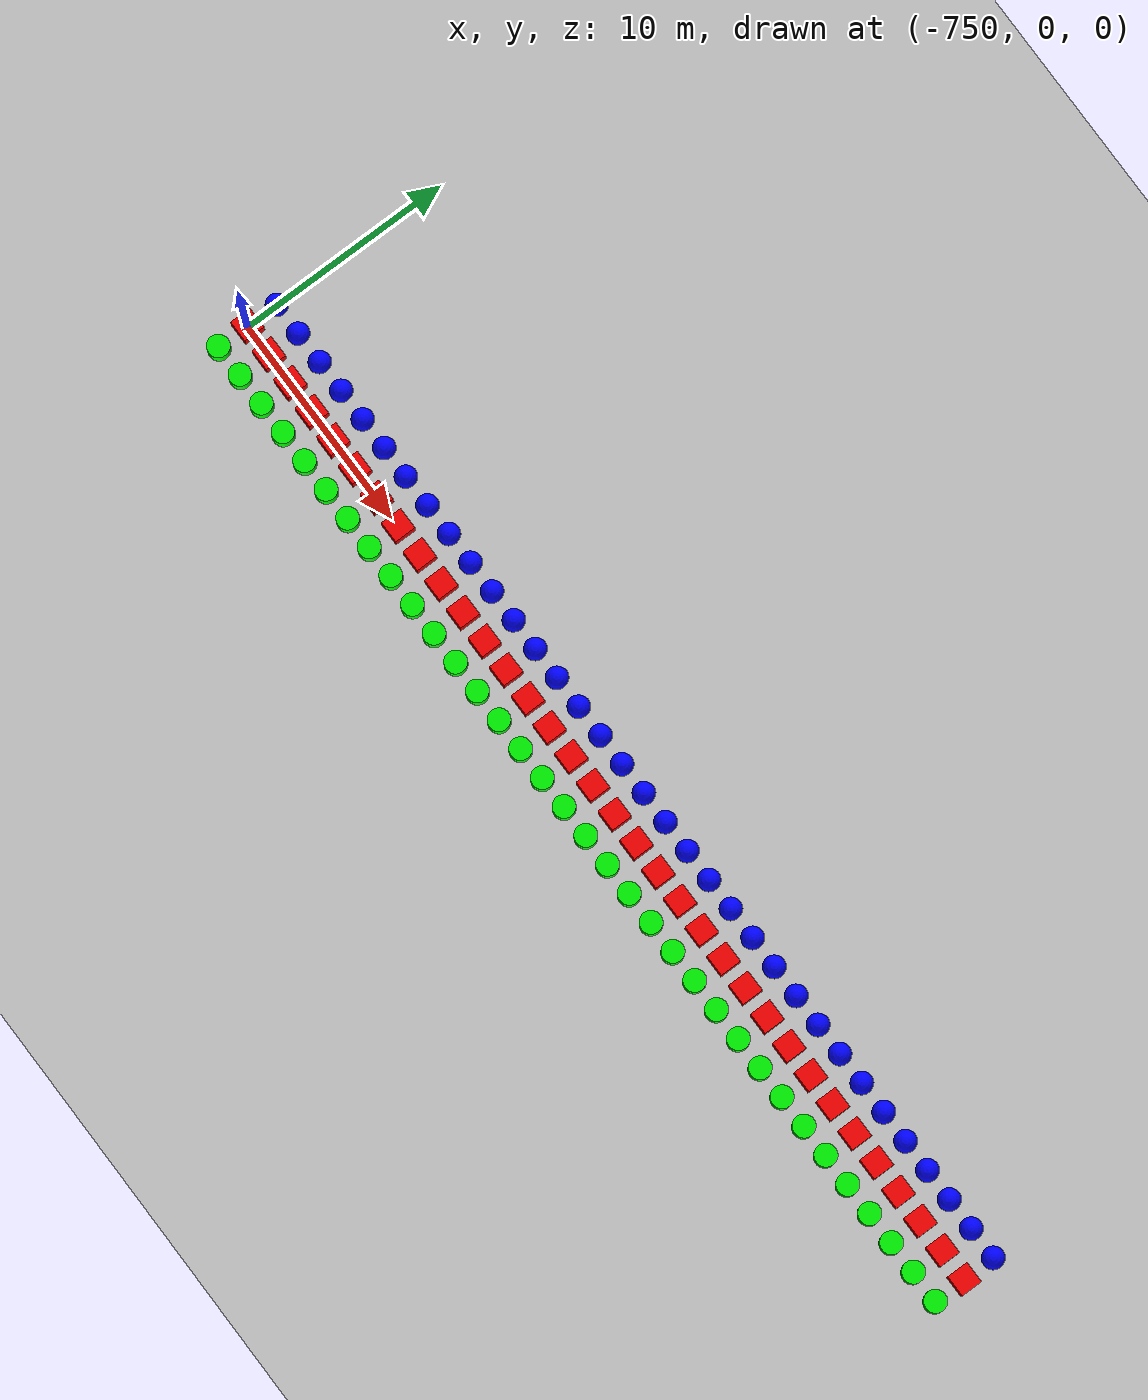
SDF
<?xml version="1.0" ?>
<!--
  To generate sdf file using this erb template, run `erb -T 1 shapes_population.sdf.erb > shapes_population.sdf`
-->
<sdf version="1.6">
  <world name="shapes">
    <physics name="1ms" type="ignored">
      <max_step_size>0.001</max_step_size>
      <real_time_factor>1.0</real_time_factor>
    </physics>
    <plugin
      filename="gz-sim-physics-system"
      name="gz::sim::systems::Physics">
    </plugin>
    <plugin
      filename="gz-sim-user-commands-system"
      name="gz::sim::systems::UserCommands">
    </plugin>
    <plugin
      filename="gz-sim-scene-broadcaster-system"
      name="gz::sim::systems::SceneBroadcaster">
    </plugin>
    <plugin
      filename="gz-sim-sensors-system"
      name="gz::sim::systems::Sensors">
      <render_engine>ogre</render_engine>
      <background_color>0.8 0.8 0.8 1.0</background_color>
    </plugin>

    <scene>
      <ambient>1.0 1.0 1.0</ambient>
      <background>0.8 0.8 0.8</background>
    </scene>

    <light type="directional" name="sun">
      <cast_shadows>true</cast_shadows>
      <pose>0 0 10 0 0 0</pose>
      <diffuse>0.8 0.8 0.8 1</diffuse>
      <specular>0.8 0.8 0.8 1</specular>
      <attenuation>
        <range>1000</range>
        <constant>0.9</constant>
        <linear>0.01</linear>
        <quadratic>0.001</quadratic>
      </attenuation>
      <direction>-0.5 0.1 -0.9</direction>
    </light>

    <model name="ground_plane">
      <static>true</static>
      <link name="link">
        <collision name="collision">
          <geometry>
            <plane>
              <normal>0 0 1</normal>
              <size>100 100</size>
            </plane>
          </geometry>
        </collision>
        <visual name="visual">
          <geometry>
            <plane>
              <normal>0 0 1</normal>
              <size>100 100</size>
            </plane>
          </geometry>
          <material>
            <ambient>0.8 0.8 0.8 1</ambient>
            <diffuse>0.8 0.8 0.8 1</diffuse>
            <specular>0.8 0.8 0.8 1</specular>
          </material>
        </visual>
      </link>
    </model>

    <model name="box_0">
      <pose>-750.0 0 0.5 0 0 0</pose>
      <link name="box_link">
        <inertial>
          <inertia>
            <ixx>1</ixx>
            <ixy>0</ixy>
            <ixz>0</ixz>
            <iyy>1</iyy>
            <iyz>0</iyz>
            <izz>1</izz>
          </inertia>
          <mass>1.0</mass>
        </inertial>
        <collision name="box_collision">
          <geometry>
            <box>
              <size>1 1 1</size>
            </box>
          </geometry>
        </collision>

        <visual name="box_visual">
          <geometry>
            <box>
              <size>1 1 1</size>
            </box>
          </geometry>
          <material>
            <ambient>1 0 0 1</ambient>
            <diffuse>1 0 0 1</diffuse>
            <specular>1 0 0 1</specular>
          </material>
        </visual>
      </link>
    </model>

    <model name="cylinder_0">
      <pose>-750.0 -1.5 0.5 0 0 0</pose>
      <link name="cylinder_link">
        <inertial>
          <inertia>
            <ixx>2</ixx>
            <ixy>0</ixy>
            <ixz>0</ixz>
            <iyy>2</iyy>
            <iyz>0</iyz>
            <izz>2</izz>
          </inertia>
          <mass>2.0</mass>
        </inertial>
        <collision name="cylinder_collision">
          <geometry>
            <cylinder>
              <radius>0.5</radius>
              <length>1.0</length>
            </cylinder>
          </geometry>
        </collision>

        <visual name="cylinder_visual">
          <geometry>
            <cylinder>
              <radius>0.5</radius>
              <length>1.0</length>
            </cylinder>
          </geometry>
          <material>
            <ambient>0 1 0 1</ambient>
            <diffuse>0 1 0 1</diffuse>
            <specular>0 1 0 1</specular>
          </material>
        </visual>
      </link>
    </model>

    <model name="sphere_0">
      <pose>-750.0 1.5 0.5 0 0 0</pose>
      <link name="sphere_link">
        <inertial>
          <inertia>
            <ixx>3</ixx>
            <ixy>0</ixy>
            <ixz>0</ixz>
            <iyy>3</iyy>
            <iyz>0</iyz>
            <izz>3</izz>
          </inertia>
          <mass>3.0</mass>
        </inertial>
        <collision name="sphere_collision">
          <geometry>
            <sphere>
              <radius>0.5</radius>
            </sphere>
          </geometry>
        </collision>

        <visual name="sphere_visual">
          <geometry>
            <sphere>
              <radius>0.5</radius>
            </sphere>
          </geometry>
          <material>
            <ambient>0 0 1 1</ambient>
            <diffuse>0 0 1 1</diffuse>
            <specular>0 0 1 1</specular>
          </material>
        </visual>
      </link>
    </model>

    <model name="box_1">
      <pose>-748.5 0 0.5 0 0 0</pose>
      <link name="box_link">
        <inertial>
          <inertia>
            <ixx>1</ixx>
            <ixy>0</ixy>
            <ixz>0</ixz>
            <iyy>1</iyy>
            <iyz>0</iyz>
            <izz>1</izz>
          </inertia>
          <mass>1.0</mass>
        </inertial>
        <collision name="box_collision">
          <geometry>
            <box>
              <size>1 1 1</size>
            </box>
          </geometry>
        </collision>

        <visual name="box_visual">
          <geometry>
            <box>
              <size>1 1 1</size>
            </box>
          </geometry>
          <material>
            <ambient>1 0 0 1</ambient>
            <diffuse>1 0 0 1</diffuse>
            <specular>1 0 0 1</specular>
          </material>
        </visual>
      </link>
    </model>

    <model name="cylinder_1">
      <pose>-748.5 -1.5 0.5 0 0 0</pose>
      <link name="cylinder_link">
        <inertial>
          <inertia>
            <ixx>2</ixx>
            <ixy>0</ixy>
            <ixz>0</ixz>
            <iyy>2</iyy>
            <iyz>0</iyz>
            <izz>2</izz>
          </inertia>
          <mass>2.0</mass>
        </inertial>
        <collision name="cylinder_collision">
          <geometry>
            <cylinder>
              <radius>0.5</radius>
              <length>1.0</length>
            </cylinder>
          </geometry>
        </collision>

        <visual name="cylinder_visual">
          <geometry>
            <cylinder>
              <radius>0.5</radius>
              <length>1.0</length>
            </cylinder>
          </geometry>
          <material>
            <ambient>0 1 0 1</ambient>
            <diffuse>0 1 0 1</diffuse>
            <specular>0 1 0 1</specular>
          </material>
        </visual>
      </link>
    </model>

    <model name="sphere_1">
      <pose>-748.5 1.5 0.5 0 0 0</pose>
      <link name="sphere_link">
        <inertial>
          <inertia>
            <ixx>3</ixx>
            <ixy>0</ixy>
            <ixz>0</ixz>
            <iyy>3</iyy>
            <iyz>0</iyz>
            <izz>3</izz>
          </inertia>
          <mass>3.0</mass>
        </inertial>
        <collision name="sphere_collision">
          <geometry>
            <sphere>
              <radius>0.5</radius>
            </sphere>
          </geometry>
        </collision>

        <visual name="sphere_visual">
          <geometry>
            <sphere>
              <radius>0.5</radius>
            </sphere>
          </geometry>
          <material>
            <ambient>0 0 1 1</ambient>
            <diffuse>0 0 1 1</diffuse>
            <specular>0 0 1 1</specular>
          </material>
        </visual>
      </link>
    </model>

    <model name="box_2">
      <pose>-747.0 0 0.5 0 0 0</pose>
      <link name="box_link">
        <inertial>
          <inertia>
            <ixx>1</ixx>
            <ixy>0</ixy>
            <ixz>0</ixz>
            <iyy>1</iyy>
            <iyz>0</iyz>
            <izz>1</izz>
          </inertia>
          <mass>1.0</mass>
        </inertial>
        <collision name="box_collision">
          <geometry>
            <box>
              <size>1 1 1</size>
            </box>
          </geometry>
        </collision>

        <visual name="box_visual">
          <geometry>
            <box>
              <size>1 1 1</size>
            </box>
          </geometry>
          <material>
            <ambient>1 0 0 1</ambient>
            <diffuse>1 0 0 1</diffuse>
            <specular>1 0 0 1</specular>
          </material>
        </visual>
      </link>
    </model>

    <model name="cylinder_2">
      <pose>-747.0 -1.5 0.5 0 0 0</pose>
      <link name="cylinder_link">
        <inertial>
          <inertia>
            <ixx>2</ixx>
            <ixy>0</ixy>
            <ixz>0</ixz>
            <iyy>2</iyy>
            <iyz>0</iyz>
            <izz>2</izz>
          </inertia>
          <mass>2.0</mass>
        </inertial>
        <collision name="cylinder_collision">
          <geometry>
            <cylinder>
              <radius>0.5</radius>
              <length>1.0</length>
            </cylinder>
          </geometry>
        </collision>

        <visual name="cylinder_visual">
          <geometry>
            <cylinder>
              <radius>0.5</radius>
              <length>1.0</length>
            </cylinder>
          </geometry>
          <material>
            <ambient>0 1 0 1</ambient>
            <diffuse>0 1 0 1</diffuse>
            <specular>0 1 0 1</specular>
          </material>
        </visual>
      </link>
    </model>

    <model name="sphere_2">
      <pose>-747.0 1.5 0.5 0 0 0</pose>
      <link name="sphere_link">
        <inertial>
          <inertia>
            <ixx>3</ixx>
            <ixy>0</ixy>
            <ixz>0</ixz>
            <iyy>3</iyy>
            <iyz>0</iyz>
            <izz>3</izz>
          </inertia>
          <mass>3.0</mass>
        </inertial>
        <collision name="sphere_collision">
          <geometry>
            <sphere>
              <radius>0.5</radius>
            </sphere>
          </geometry>
        </collision>

        <visual name="sphere_visual">
          <geometry>
            <sphere>
              <radius>0.5</radius>
            </sphere>
          </geometry>
          <material>
            <ambient>0 0 1 1</ambient>
            <diffuse>0 0 1 1</diffuse>
            <specular>0 0 1 1</specular>
          </material>
        </visual>
      </link>
    </model>

    <model name="box_3">
      <pose>-745.5 0 0.5 0 0 0</pose>
      <link name="box_link">
        <inertial>
          <inertia>
            <ixx>1</ixx>
            <ixy>0</ixy>
            <ixz>0</ixz>
            <iyy>1</iyy>
            <iyz>0</iyz>
            <izz>1</izz>
          </inertia>
          <mass>1.0</mass>
        </inertial>
        <collision name="box_collision">
          <geometry>
            <box>
              <size>1 1 1</size>
            </box>
          </geometry>
        </collision>

        <visual name="box_visual">
          <geometry>
            <box>
              <size>1 1 1</size>
            </box>
          </geometry>
          <material>
            <ambient>1 0 0 1</ambient>
            <diffuse>1 0 0 1</diffuse>
            <specular>1 0 0 1</specular>
          </material>
        </visual>
      </link>
    </model>

    <model name="cylinder_3">
      <pose>-745.5 -1.5 0.5 0 0 0</pose>
      <link name="cylinder_link">
        <inertial>
          <inertia>
            <ixx>2</ixx>
            <ixy>0</ixy>
            <ixz>0</ixz>
            <iyy>2</iyy>
            <iyz>0</iyz>
            <izz>2</izz>
          </inertia>
          <mass>2.0</mass>
        </inertial>
        <collision name="cylinder_collision">
          <geometry>
            <cylinder>
              <radius>0.5</radius>
              <length>1.0</length>
            </cylinder>
          </geometry>
        </collision>

        <visual name="cylinder_visual">
          <geometry>
            <cylinder>
              <radius>0.5</radius>
              <length>1.0</length>
            </cylinder>
          </geometry>
          <material>
            <ambient>0 1 0 1</ambient>
            <diffuse>0 1 0 1</diffuse>
            <specular>0 1 0 1</specular>
          </material>
        </visual>
      </link>
    </model>

    <model name="sphere_3">
      <pose>-745.5 1.5 0.5 0 0 0</pose>
      <link name="sphere_link">
        <inertial>
          <inertia>
            <ixx>3</ixx>
            <ixy>0</ixy>
            <ixz>0</ixz>
            <iyy>3</iyy>
            <iyz>0</iyz>
            <izz>3</izz>
          </inertia>
          <mass>3.0</mass>
        </inertial>
        <collision name="sphere_collision">
          <geometry>
            <sphere>
              <radius>0.5</radius>
            </sphere>
          </geometry>
        </collision>

        <visual name="sphere_visual">
          <geometry>
            <sphere>
              <radius>0.5</radius>
            </sphere>
          </geometry>
          <material>
            <ambient>0 0 1 1</ambient>
            <diffuse>0 0 1 1</diffuse>
            <specular>0 0 1 1</specular>
          </material>
        </visual>
      </link>
    </model>

    <model name="box_4">
      <pose>-744.0 0 0.5 0 0 0</pose>
      <link name="box_link">
        <inertial>
          <inertia>
            <ixx>1</ixx>
            <ixy>0</ixy>
            <ixz>0</ixz>
            <iyy>1</iyy>
            <iyz>0</iyz>
            <izz>1</izz>
          </inertia>
          <mass>1.0</mass>
        </inertial>
        <collision name="box_collision">
          <geometry>
            <box>
              <size>1 1 1</size>
            </box>
          </geometry>
        </collision>

        <visual name="box_visual">
          <geometry>
            <box>
              <size>1 1 1</size>
            </box>
          </geometry>
          <material>
            <ambient>1 0 0 1</ambient>
            <diffuse>1 0 0 1</diffuse>
            <specular>1 0 0 1</specular>
          </material>
        </visual>
      </link>
    </model>

    <model name="cylinder_4">
      <pose>-744.0 -1.5 0.5 0 0 0</pose>
      <link name="cylinder_link">
        <inertial>
          <inertia>
            <ixx>2</ixx>
            <ixy>0</ixy>
            <ixz>0</ixz>
            <iyy>2</iyy>
            <iyz>0</iyz>
            <izz>2</izz>
          </inertia>
          <mass>2.0</mass>
        </inertial>
        <collision name="cylinder_collision">
          <geometry>
            <cylinder>
              <radius>0.5</radius>
              <length>1.0</length>
            </cylinder>
          </geometry>
        </collision>

        <visual name="cylinder_visual">
          <geometry>
            <cylinder>
              <radius>0.5</radius>
              <length>1.0</length>
            </cylinder>
          </geometry>
          <material>
            <ambient>0 1 0 1</ambient>
            <diffuse>0 1 0 1</diffuse>
            <specular>0 1 0 1</specular>
          </material>
        </visual>
      </link>
    </model>

    <model name="sphere_4">
      <pose>-744.0 1.5 0.5 0 0 0</pose>
      <link name="sphere_link">
        <inertial>
          <inertia>
            <ixx>3</ixx>
            <ixy>0</ixy>
            <ixz>0</ixz>
            <iyy>3</iyy>
            <iyz>0</iyz>
            <izz>3</izz>
          </inertia>
          <mass>3.0</mass>
        </inertial>
        <collision name="sphere_collision">
          <geometry>
            <sphere>
              <radius>0.5</radius>
            </sphere>
          </geometry>
        </collision>

        <visual name="sphere_visual">
          <geometry>
            <sphere>
              <radius>0.5</radius>
            </sphere>
          </geometry>
          <material>
            <ambient>0 0 1 1</ambient>
            <diffuse>0 0 1 1</diffuse>
            <specular>0 0 1 1</specular>
          </material>
        </visual>
      </link>
    </model>

    <model name="box_5">
      <pose>-742.5 0 0.5 0 0 0</pose>
      <link name="box_link">
        <inertial>
          <inertia>
            <ixx>1</ixx>
            <ixy>0</ixy>
            <ixz>0</ixz>
            <iyy>1</iyy>
            <iyz>0</iyz>
            <izz>1</izz>
          </inertia>
          <mass>1.0</mass>
        </inertial>
        <collision name="box_collision">
          <geometry>
            <box>
              <size>1 1 1</size>
            </box>
          </geometry>
        </collision>

        <visual name="box_visual">
          <geometry>
            <box>
              <size>1 1 1</size>
            </box>
          </geometry>
          <material>
            <ambient>1 0 0 1</ambient>
            <diffuse>1 0 0 1</diffuse>
            <specular>1 0 0 1</specular>
          </material>
        </visual>
      </link>
    </model>

    <model name="cylinder_5">
      <pose>-742.5 -1.5 0.5 0 0 0</pose>
      <link name="cylinder_link">
        <inertial>
          <inertia>
            <ixx>2</ixx>
            <ixy>0</ixy>
            <ixz>0</ixz>
            <iyy>2</iyy>
            <iyz>0</iyz>
            <izz>2</izz>
          </inertia>
          <mass>2.0</mass>
        </inertial>
        <collision name="cylinder_collision">
          <geometry>
            <cylinder>
              <radius>0.5</radius>
              <length>1.0</length>
            </cylinder>
          </geometry>
        </collision>

        <visual name="cylinder_visual">
          <geometry>
            <cylinder>
              <radius>0.5</radius>
              <length>1.0</length>
            </cylinder>
          </geometry>
          <material>
            <ambient>0 1 0 1</ambient>
            <diffuse>0 1 0 1</diffuse>
            <specular>0 1 0 1</specular>
          </material>
        </visual>
      </link>
    </model>

    <model name="sphere_5">
      <pose>-742.5 1.5 0.5 0 0 0</pose>
      <link name="sphere_link">
        <inertial>
          <inertia>
            <ixx>3</ixx>
            <ixy>0</ixy>
            <ixz>0</ixz>
            <iyy>3</iyy>
            <iyz>0</iyz>
            <izz>3</izz>
          </inertia>
          <mass>3.0</mass>
        </inertial>
        <collision name="sphere_collision">
          <geometry>
            <sphere>
              <radius>0.5</radius>
            </sphere>
          </geometry>
        </collision>

        <visual name="sphere_visual">
          <geometry>
            <sphere>
              <radius>0.5</radius>
            </sphere>
          </geometry>
          <material>
            <ambient>0 0 1 1</ambient>
            <diffuse>0 0 1 1</diffuse>
            <specular>0 0 1 1</specular>
          </material>
        </visual>
      </link>
    </model>

    <model name="box_6">
      <pose>-741.0 0 0.5 0 0 0</pose>
      <link name="box_link">
        <inertial>
          <inertia>
            <ixx>1</ixx>
            <ixy>0</ixy>
            <ixz>0</ixz>
            <iyy>1</iyy>
            <iyz>0</iyz>
            <izz>1</izz>
          </inertia>
          <mass>1.0</mass>
        </inertial>
        <collision name="box_collision">
          <geometry>
            <box>
              <size>1 1 1</size>
            </box>
          </geometry>
        </collision>

        <visual name="box_visual">
          <geometry>
            <box>
              <size>1 1 1</size>
            </box>
          </geometry>
          <material>
            <ambient>1 0 0 1</ambient>
            <diffuse>1 0 0 1</diffuse>
            <specular>1 0 0 1</specular>
          </material>
        </visual>
      </link>
    </model>

    <model name="cylinder_6">
      <pose>-741.0 -1.5 0.5 0 0 0</pose>
      <link name="cylinder_link">
        <inertial>
          <inertia>
            <ixx>2</ixx>
            <ixy>0</ixy>
            <ixz>0</ixz>
            <iyy>2</iyy>
            <iyz>0</iyz>
            <izz>2</izz>
          </inertia>
          <mass>2.0</mass>
        </inertial>
        <collision name="cylinder_collision">
          <geometry>
            <cylinder>
              <radius>0.5</radius>
              <length>1.0</length>
            </cylinder>
          </geometry>
        </collision>

        <visual name="cylinder_visual">
          <geometry>
            <cylinder>
              <radius>0.5</radius>
              <length>1.0</length>
            </cylinder>
          </geometry>
          <material>
            <ambient>0 1 0 1</ambient>
            <diffuse>0 1 0 1</diffuse>
            <specular>0 1 0 1</specular>
          </material>
        </visual>
      </link>
    </model>

    <model name="sphere_6">
      <pose>-741.0 1.5 0.5 0 0 0</pose>
      <link name="sphere_link">
        <inertial>
          <inertia>
            <ixx>3</ixx>
            <ixy>0</ixy>
            <ixz>0</ixz>
            <iyy>3</iyy>
            <iyz>0</iyz>
            <izz>3</izz>
          </inertia>
          <mass>3.0</mass>
        </inertial>
        <collision name="sphere_collision">
          <geometry>
            <sphere>
              <radius>0.5</radius>
            </sphere>
          </geometry>
        </collision>

        <visual name="sphere_visual">
          <geometry>
            <sphere>
              <radius>0.5</radius>
            </sphere>
          </geometry>
          <material>
            <ambient>0 0 1 1</ambient>
            <diffuse>0 0 1 1</diffuse>
            <specular>0 0 1 1</specular>
          </material>
        </visual>
      </link>
    </model>

    <model name="box_7">
      <pose>-739.5 0 0.5 0 0 0</pose>
      <link name="box_link">
        <inertial>
          <inertia>
            <ixx>1</ixx>
            <ixy>0</ixy>
            <ixz>0</ixz>
            <iyy>1</iyy>
            <iyz>0</iyz>
            <izz>1</izz>
          </inertia>
          <mass>1.0</mass>
        </inertial>
        <collision name="box_collision">
          <geometry>
            <box>
              <size>1 1 1</size>
            </box>
          </geometry>
        </collision>

        <visual name="box_visual">
          <geometry>
            <box>
              <size>1 1 1</size>
            </box>
          </geometry>
          <material>
            <ambient>1 0 0 1</ambient>
            <diffuse>1 0 0 1</diffuse>
            <specular>1 0 0 1</specular>
          </material>
        </visual>
      </link>
    </model>

    <model name="cylinder_7">
      <pose>-739.5 -1.5 0.5 0 0 0</pose>
      <link name="cylinder_link">
        <inertial>
          <inertia>
            <ixx>2</ixx>
            <ixy>0</ixy>
            <ixz>0</ixz>
            <iyy>2</iyy>
            <iyz>0</iyz>
            <izz>2</izz>
          </inertia>
          <mass>2.0</mass>
        </inertial>
        <collision name="cylinder_collision">
          <geometry>
            <cylinder>
              <radius>0.5</radius>
              <length>1.0</length>
            </cylinder>
          </geometry>
        </collision>

        <visual name="cylinder_visual">
          <geometry>
            <cylinder>
              <radius>0.5</radius>
              <length>1.0</length>
            </cylinder>
          </geometry>
          <material>
            <ambient>0 1 0 1</ambient>
            <diffuse>0 1 0 1</diffuse>
            <specular>0 1 0 1</specular>
          </material>
        </visual>
      </link>
    </model>

    <model name="sphere_7">
      <pose>-739.5 1.5 0.5 0 0 0</pose>
      <link name="sphere_link">
        <inertial>
          <inertia>
            <ixx>3</ixx>
            <ixy>0</ixy>
            <ixz>0</ixz>
            <iyy>3</iyy>
            <iyz>0</iyz>
            <izz>3</izz>
          </inertia>
          <mass>3.0</mass>
        </inertial>
        <collision name="sphere_collision">
          <geometry>
            <sphere>
              <radius>0.5</radius>
            </sphere>
          </geometry>
        </collision>

        <visual name="sphere_visual">
          <geometry>
            <sphere>
              <radius>0.5</radius>
            </sphere>
          </geometry>
          <material>
            <ambient>0 0 1 1</ambient>
            <diffuse>0 0 1 1</diffuse>
            <specular>0 0 1 1</specular>
          </material>
        </visual>
      </link>
    </model>

    <model name="box_8">
      <pose>-738.0 0 0.5 0 0 0</pose>
      <link name="box_link">
        <inertial>
          <inertia>
            <ixx>1</ixx>
            <ixy>0</ixy>
            <ixz>0</ixz>
            <iyy>1</iyy>
            <iyz>0</iyz>
            <izz>1</izz>
          </inertia>
          <mass>1.0</mass>
        </inertial>
        <collision name="box_collision">
          <geometry>
            <box>
              <size>1 1 1</size>
            </box>
          </geometry>
        </collision>

        <visual name="box_visual">
          <geometry>
            <box>
              <size>1 1 1</size>
            </box>
          </geometry>
          <material>
            <ambient>1 0 0 1</ambient>
            <diffuse>1 0 0 1</diffuse>
            <specular>1 0 0 1</specular>
          </material>
        </visual>
      </link>
    </model>

    <model name="cylinder_8">
      <pose>-738.0 -1.5 0.5 0 0 0</pose>
      <link name="cylinder_link">
        <inertial>
          <inertia>
            <ixx>2</ixx>
            <ixy>0</ixy>
            <ixz>0</ixz>
            <iyy>2</iyy>
            <iyz>0</iyz>
            <izz>2</izz>
          </inertia>
          <mass>2.0</mass>
        </inertial>
        <collision name="cylinder_collision">
          <geometry>
            <cylinder>
              <radius>0.5</radius>
              <length>1.0</length>
            </cylinder>
          </geometry>
        </collision>

        <visual name="cylinder_visual">
          <geometry>
            <cylinder>
              <radius>0.5</radius>
              <length>1.0</length>
            </cylinder>
          </geometry>
          <material>
            <ambient>0 1 0 1</ambient>
            <diffuse>0 1 0 1</diffuse>
            <specular>0 1 0 1</specular>
          </material>
        </visual>
      </link>
    </model>

    <model name="sphere_8">
      <pose>-738.0 1.5 0.5 0 0 0</pose>
      <link name="sphere_link">
        <inertial>
          <inertia>
            <ixx>3</ixx>
            <ixy>0</ixy>
            <ixz>0</ixz>
            <iyy>3</iyy>
            <iyz>0</iyz>
            <izz>3</izz>
          </inertia>
          <mass>3.0</mass>
        </inertial>
        <collision name="sphere_collision">
          <geometry>
            <sphere>
              <radius>0.5</radius>
            </sphere>
          </geometry>
        </collision>

        <visual name="sphere_visual">
          <geometry>
            <sphere>
              <radius>0.5</radius>
            </sphere>
          </geometry>
          <material>
            <ambient>0 0 1 1</ambient>
            <diffuse>0 0 1 1</diffuse>
            <specular>0 0 1 1</specular>
          </material>
        </visual>
      </link>
    </model>

    <model name="box_9">
      <pose>-736.5 0 0.5 0 0 0</pose>
      <link name="box_link">
        <inertial>
          <inertia>
            <ixx>1</ixx>
            <ixy>0</ixy>
            <ixz>0</ixz>
            <iyy>1</iyy>
            <iyz>0</iyz>
            <izz>1</izz>
          </inertia>
          <mass>1.0</mass>
        </inertial>
        <collision name="box_collision">
          <geometry>
            <box>
              <size>1 1 1</size>
            </box>
          </geometry>
        </collision>

        <visual name="box_visual">
          <geometry>
            <box>
              <size>1 1 1</size>
            </box>
          </geometry>
          <material>
            <ambient>1 0 0 1</ambient>
            <diffuse>1 0 0 1</diffuse>
            <specular>1 0 0 1</specular>
          </material>
        </visual>
      </link>
    </model>

    <model name="cylinder_9">
      <pose>-736.5 -1.5 0.5 0 0 0</pose>
      <link name="cylinder_link">
        <inertial>
          <inertia>
            <ixx>2</ixx>
            <ixy>0</ixy>
            <ixz>0</ixz>
            <iyy>2</iyy>
            <iyz>0</iyz>
            <izz>2</izz>
          </inertia>
          <mass>2.0</mass>
        </inertial>
        <collision name="cylinder_collision">
          <geometry>
            <cylinder>
              <radius>0.5</radius>
              <length>1.0</length>
            </cylinder>
          </geometry>
        </collision>

        <visual name="cylinder_visual">
          <geometry>
            <cylinder>
              <radius>0.5</radius>
              <length>1.0</length>
            </cylinder>
          </geometry>
          <material>
            <ambient>0 1 0 1</ambient>
            <diffuse>0 1 0 1</diffuse>
            <specular>0 1 0 1</specular>
          </material>
        </visual>
      </link>
    </model>

    <model name="sphere_9">
      <pose>-736.5 1.5 0.5 0 0 0</pose>
      <link name="sphere_link">
        <inertial>
          <inertia>
            <ixx>3</ixx>
            <ixy>0</ixy>
            <ixz>0</ixz>
            <iyy>3</iyy>
            <iyz>0</iyz>
            <izz>3</izz>
          </inertia>
          <mass>3.0</mass>
        </inertial>
        <collision name="sphere_collision">
          <geometry>
            <sphere>
              <radius>0.5</radius>
            </sphere>
          </geometry>
        </collision>

        <visual name="sphere_visual">
          <geometry>
            <sphere>
              <radius>0.5</radius>
            </sphere>
          </geometry>
          <material>
            <ambient>0 0 1 1</ambient>
            <diffuse>0 0 1 1</diffuse>
            <specular>0 0 1 1</specular>
          </material>
        </visual>
      </link>
    </model>

    <model name="box_10">
      <pose>-735.0 0 0.5 0 0 0</pose>
      <link name="box_link">
        <inertial>
          <inertia>
            <ixx>1</ixx>
            <ixy>0</ixy>
            <ixz>0</ixz>
            <iyy>1</iyy>
            <iyz>0</iyz>
            <izz>1</izz>
          </inertia>
          <mass>1.0</mass>
        </inertial>
        <collision name="box_collision">
          <geometry>
            <box>
              <size>1 1 1</size>
            </box>
          </geometry>
        </collision>

        <visual name="box_visual">
          <geometry>
            <box>
              <size>1 1 1</size>
            </box>
          </geometry>
          <material>
            <ambient>1 0 0 1</ambient>
            <diffuse>1 0 0 1</diffuse>
            <specular>1 0 0 1</specular>
          </material>
        </visual>
      </link>
    </model>

    <model name="cylinder_10">
      <pose>-735.0 -1.5 0.5 0 0 0</pose>
      <link name="cylinder_link">
        <inertial>
          <inertia>
            <ixx>2</ixx>
            <ixy>0</ixy>
            <ixz>0</ixz>
            <iyy>2</iyy>
            <iyz>0</iyz>
            <izz>2</izz>
          </inertia>
          <mass>2.0</mass>
        </inertial>
        <collision name="cylinder_collision">
          <geometry>
            <cylinder>
              <radius>0.5</radius>
              <length>1.0</length>
            </cylinder>
          </geometry>
        </collision>

        <visual name="cylinder_visual">
          <geometry>
            <cylinder>
              <radius>0.5</radius>
              <length>1.0</length>
            </cylinder>
          </geometry>
          <material>
            <ambient>0 1 0 1</ambient>
            <diffuse>0 1 0 1</diffuse>
            <specular>0 1 0 1</specular>
          </material>
        </visual>
      </link>
    </model>

    <model name="sphere_10">
      <pose>-735.0 1.5 0.5 0 0 0</pose>
      <link name="sphere_link">
        <inertial>
          <inertia>
            <ixx>3</ixx>
            <ixy>0</ixy>
            <ixz>0</ixz>
            <iyy>3</iyy>
            <iyz>0</iyz>
            <izz>3</izz>
          </inertia>
          <mass>3.0</mass>
        </inertial>
        <collision name="sphere_collision">
          <geometry>
            <sphere>
              <radius>0.5</radius>
            </sphere>
          </geometry>
        </collision>

        <visual name="sphere_visual">
          <geometry>
            <sphere>
              <radius>0.5</radius>
            </sphere>
          </geometry>
          <material>
            <ambient>0 0 1 1</ambient>
            <diffuse>0 0 1 1</diffuse>
            <specular>0 0 1 1</specular>
          </material>
        </visual>
      </link>
    </model>

    <model name="box_11">
      <pose>-733.5 0 0.5 0 0 0</pose>
      <link name="box_link">
        <inertial>
          <inertia>
            <ixx>1</ixx>
            <ixy>0</ixy>
            <ixz>0</ixz>
            <iyy>1</iyy>
            <iyz>0</iyz>
            <izz>1</izz>
          </inertia>
          <mass>1.0</mass>
        </inertial>
        <collision name="box_collision">
          <geometry>
            <box>
              <size>1 1 1</size>
            </box>
          </geometry>
        </collision>

        <visual name="box_visual">
          <geometry>
            <box>
              <size>1 1 1</size>
            </box>
          </geometry>
          <material>
            <ambient>1 0 0 1</ambient>
            <diffuse>1 0 0 1</diffuse>
            <specular>1 0 0 1</specular>
          </material>
        </visual>
      </link>
    </model>

    <model name="cylinder_11">
      <pose>-733.5 -1.5 0.5 0 0 0</pose>
      <link name="cylinder_link">
        <inertial>
          <inertia>
            <ixx>2</ixx>
            <ixy>0</ixy>
            <ixz>0</ixz>
            <iyy>2</iyy>
            <iyz>0</iyz>
            <izz>2</izz>
          </inertia>
          <mass>2.0</mass>
        </inertial>
        <collision name="cylinder_collision">
          <geometry>
            <cylinder>
              <radius>0.5</radius>
              <length>1.0</length>
            </cylinder>
          </geometry>
        </collision>

        <visual name="cylinder_visual">
          <geometry>
            <cylinder>
              <radius>0.5</radius>
              <length>1.0</length>
            </cylinder>
          </geometry>
          <material>
            <ambient>0 1 0 1</ambient>
            <diffuse>0 1 0 1</diffuse>
            <specular>0 1 0 1</specular>
          </material>
        </visual>
      </link>
    </model>

    <model name="sphere_11">
      <pose>-733.5 1.5 0.5 0 0 0</pose>
      <link name="sphere_link">
        <inertial>
          <inertia>
            <ixx>3</ixx>
            <ixy>0</ixy>
            <ixz>0</ixz>
            <iyy>3</iyy>
            <iyz>0</iyz>
            <izz>3</izz>
          </inertia>
          <mass>3.0</mass>
        </inertial>
        <collision name="sphere_collision">
          <geometry>
            <sphere>
              <radius>0.5</radius>
            </sphere>
          </geometry>
        </collision>

        <visual name="sphere_visual">
          <geometry>
            <sphere>
              <radius>0.5</radius>
            </sphere>
          </geometry>
          <material>
            <ambient>0 0 1 1</ambient>
            <diffuse>0 0 1 1</diffuse>
            <specular>0 0 1 1</specular>
          </material>
        </visual>
      </link>
    </model>

    <model name="box_12">
      <pose>-732.0 0 0.5 0 0 0</pose>
      <link name="box_link">
        <inertial>
          <inertia>
            <ixx>1</ixx>
            <ixy>0</ixy>
            <ixz>0</ixz>
            <iyy>1</iyy>
            <iyz>0</iyz>
            <izz>1</izz>
          </inertia>
          <mass>1.0</mass>
        </inertial>
        <collision name="box_collision">
          <geometry>
            <box>
              <size>1 1 1</size>
            </box>
          </geometry>
        </collision>

        <visual name="box_visual">
          <geometry>
            <box>
              <size>1 1 1</size>
            </box>
          </geometry>
          <material>
            <ambient>1 0 0 1</ambient>
            <diffuse>1 0 0 1</diffuse>
            <specular>1 0 0 1</specular>
          </material>
        </visual>
      </link>
    </model>

    <model name="cylinder_12">
      <pose>-732.0 -1.5 0.5 0 0 0</pose>
      <link name="cylinder_link">
        <inertial>
          <inertia>
            <ixx>2</ixx>
            <ixy>0</ixy>
            <ixz>0</ixz>
            <iyy>2</iyy>
            <iyz>0</iyz>
            <izz>2</izz>
          </inertia>
          <mass>2.0</mass>
        </inertial>
        <collision name="cylinder_collision">
          <geometry>
            <cylinder>
              <radius>0.5</radius>
              <length>1.0</length>
            </cylinder>
          </geometry>
        </collision>

        <visual name="cylinder_visual">
          <geometry>
            <cylinder>
              <radius>0.5</radius>
              <length>1.0</length>
            </cylinder>
          </geometry>
          <material>
            <ambient>0 1 0 1</ambient>
            <diffuse>0 1 0 1</diffuse>
            <specular>0 1 0 1</specular>
          </material>
        </visual>
      </link>
    </model>

    <model name="sphere_12">
      <pose>-732.0 1.5 0.5 0 0 0</pose>
      <link name="sphere_link">
        <inertial>
          <inertia>
            <ixx>3</ixx>
            <ixy>0</ixy>
            <ixz>0</ixz>
            <iyy>3</iyy>
            <iyz>0</iyz>
            <izz>3</izz>
          </inertia>
          <mass>3.0</mass>
        </inertial>
        <collision name="sphere_collision">
          <geometry>
            <sphere>
              <radius>0.5</radius>
            </sphere>
          </geometry>
        </collision>

        <visual name="sphere_visual">
          <geometry>
            <sphere>
              <radius>0.5</radius>
            </sphere>
          </geometry>
          <material>
            <ambient>0 0 1 1</ambient>
            <diffuse>0 0 1 1</diffuse>
            <specular>0 0 1 1</specular>
          </material>
        </visual>
      </link>
    </model>

    <model name="box_13">
      <pose>-730.5 0 0.5 0 0 0</pose>
      <link name="box_link">
        <inertial>
          <inertia>
            <ixx>1</ixx>
            <ixy>0</ixy>
            <ixz>0</ixz>
            <iyy>1</iyy>
            <iyz>0</iyz>
            <izz>1</izz>
          </inertia>
          <mass>1.0</mass>
        </inertial>
        <collision name="box_collision">
          <geometry>
            <box>
              <size>1 1 1</size>
            </box>
          </geometry>
        </collision>

        <visual name="box_visual">
          <geometry>
            <box>
              <size>1 1 1</size>
            </box>
          </geometry>
          <material>
            <ambient>1 0 0 1</ambient>
            <diffuse>1 0 0 1</diffuse>
            <specular>1 0 0 1</specular>
          </material>
        </visual>
      </link>
    </model>

    <model name="cylinder_13">
      <pose>-730.5 -1.5 0.5 0 0 0</pose>
      <link name="cylinder_link">
        <inertial>
          <inertia>
            <ixx>2</ixx>
            <ixy>0</ixy>
            <ixz>0</ixz>
            <iyy>2</iyy>
            <iyz>0</iyz>
            <izz>2</izz>
          </inertia>
          <mass>2.0</mass>
        </inertial>
        <collision name="cylinder_collision">
          <geometry>
            <cylinder>
              <radius>0.5</radius>
              <length>1.0</length>
            </cylinder>
          </geometry>
        </collision>

        <visual name="cylinder_visual">
          <geometry>
            <cylinder>
              <radius>0.5</radius>
              <length>1.0</length>
            </cylinder>
          </geometry>
          <material>
            <ambient>0 1 0 1</ambient>
            <diffuse>0 1 0 1</diffuse>
            <specular>0 1 0 1</specular>
          </material>
        </visual>
      </link>
    </model>

    <model name="sphere_13">
      <pose>-730.5 1.5 0.5 0 0 0</pose>
      <link name="sphere_link">
        <inertial>
          <inertia>
            <ixx>3</ixx>
            <ixy>0</ixy>
            <ixz>0</ixz>
            <iyy>3</iyy>
            <iyz>0</iyz>
            <izz>3</izz>
          </inertia>
          <mass>3.0</mass>
        </inertial>
        <collision name="sphere_collision">
          <geometry>
            <sphere>
              <radius>0.5</radius>
            </sphere>
          </geometry>
        </collision>

        <visual name="sphere_visual">
          <geometry>
            <sphere>
              <radius>0.5</radius>
            </sphere>
          </geometry>
          <material>
            <ambient>0 0 1 1</ambient>
            <diffuse>0 0 1 1</diffuse>
            <specular>0 0 1 1</specular>
          </material>
        </visual>
      </link>
    </model>

    <model name="box_14">
      <pose>-729.0 0 0.5 0 0 0</pose>
      <link name="box_link">
        <inertial>
          <inertia>
            <ixx>1</ixx>
            <ixy>0</ixy>
            <ixz>0</ixz>
            <iyy>1</iyy>
            <iyz>0</iyz>
            <izz>1</izz>
          </inertia>
          <mass>1.0</mass>
        </inertial>
        <collision name="box_collision">
          <geometry>
            <box>
              <size>1 1 1</size>
            </box>
          </geometry>
        </collision>

        <visual name="box_visual">
          <geometry>
            <box>
              <size>1 1 1</size>
            </box>
          </geometry>
          <material>
            <ambient>1 0 0 1</ambient>
            <diffuse>1 0 0 1</diffuse>
            <specular>1 0 0 1</specular>
          </material>
        </visual>
      </link>
    </model>

    <model name="cylinder_14">
      <pose>-729.0 -1.5 0.5 0 0 0</pose>
      <link name="cylinder_link">
        <inertial>
          <inertia>
            <ixx>2</ixx>
            <ixy>0</ixy>
            <ixz>0</ixz>
            <iyy>2</iyy>
            <iyz>0</iyz>
            <izz>2</izz>
          </inertia>
          <mass>2.0</mass>
        </inertial>
        <collision name="cylinder_collision">
          <geometry>
            <cylinder>
              <radius>0.5</radius>
              <length>1.0</length>
            </cylinder>
          </geometry>
        </collision>

        <visual name="cylinder_visual">
          <geometry>
            <cylinder>
              <radius>0.5</radius>
              <length>1.0</length>
            </cylinder>
          </geometry>
          <material>
            <ambient>0 1 0 1</ambient>
            <diffuse>0 1 0 1</diffuse>
            <specular>0 1 0 1</specular>
          </material>
        </visual>
      </link>
    </model>

    <model name="sphere_14">
      <pose>-729.0 1.5 0.5 0 0 0</pose>
      <link name="sphere_link">
        <inertial>
          <inertia>
            <ixx>3</ixx>
            <ixy>0</ixy>
            <ixz>0</ixz>
            <iyy>3</iyy>
            <iyz>0</iyz>
            <izz>3</izz>
          </inertia>
          <mass>3.0</mass>
        </inertial>
        <collision name="sphere_collision">
          <geometry>
            <sphere>
              <radius>0.5</radius>
            </sphere>
          </geometry>
        </collision>

        <visual name="sphere_visual">
          <geometry>
            <sphere>
              <radius>0.5</radius>
            </sphere>
          </geometry>
          <material>
            <ambient>0 0 1 1</ambient>
            <diffuse>0 0 1 1</diffuse>
            <specular>0 0 1 1</specular>
          </material>
        </visual>
      </link>
    </model>

    <model name="box_15">
      <pose>-727.5 0 0.5 0 0 0</pose>
      <link name="box_link">
        <inertial>
          <inertia>
            <ixx>1</ixx>
            <ixy>0</ixy>
            <ixz>0</ixz>
            <iyy>1</iyy>
            <iyz>0</iyz>
            <izz>1</izz>
          </inertia>
          <mass>1.0</mass>
        </inertial>
        <collision name="box_collision">
          <geometry>
            <box>
              <size>1 1 1</size>
            </box>
          </geometry>
        </collision>

        <visual name="box_visual">
          <geometry>
            <box>
              <size>1 1 1</size>
            </box>
          </geometry>
          <material>
            <ambient>1 0 0 1</ambient>
            <diffuse>1 0 0 1</diffuse>
            <specular>1 0 0 1</specular>
          </material>
        </visual>
      </link>
    </model>

    <model name="cylinder_15">
      <pose>-727.5 -1.5 0.5 0 0 0</pose>
      <link name="cylinder_link">
        <inertial>
          <inertia>
            <ixx>2</ixx>
            <ixy>0</ixy>
            <ixz>0</ixz>
            <iyy>2</iyy>
            <iyz>0</iyz>
            <izz>2</izz>
          </inertia>
          <mass>2.0</mass>
        </inertial>
        <collision name="cylinder_collision">
          <geometry>
            <cylinder>
              <radius>0.5</radius>
              <length>1.0</length>
            </cylinder>
          </geometry>
        </collision>

        <visual name="cylinder_visual">
          <geometry>
            <cylinder>
              <radius>0.5</radius>
              <length>1.0</length>
            </cylinder>
          </geometry>
          <material>
            <ambient>0 1 0 1</ambient>
            <diffuse>0 1 0 1</diffuse>
            <specular>0 1 0 1</specular>
          </material>
        </visual>
      </link>
    </model>

    <model name="sphere_15">
      <pose>-727.5 1.5 0.5 0 0 0</pose>
      <link name="sphere_link">
        <inertial>
          <inertia>
            <ixx>3</ixx>
            <ixy>0</ixy>
            <ixz>0</ixz>
            <iyy>3</iyy>
            <iyz>0</iyz>
            <izz>3</izz>
          </inertia>
          <mass>3.0</mass>
        </inertial>
        <collision name="sphere_collision">
          <geometry>
            <sphere>
              <radius>0.5</radius>
            </sphere>
          </geometry>
        </collision>

        <visual name="sphere_visual">
          <geometry>
            <sphere>
              <radius>0.5</radius>
            </sphere>
          </geometry>
          <material>
            <ambient>0 0 1 1</ambient>
            <diffuse>0 0 1 1</diffuse>
            <specular>0 0 1 1</specular>
          </material>
        </visual>
      </link>
    </model>

    <model name="box_16">
      <pose>-726.0 0 0.5 0 0 0</pose>
      <link name="box_link">
        <inertial>
          <inertia>
            <ixx>1</ixx>
            <ixy>0</ixy>
            <ixz>0</ixz>
            <iyy>1</iyy>
            <iyz>0</iyz>
            <izz>1</izz>
          </inertia>
          <mass>1.0</mass>
        </inertial>
        <collision name="box_collision">
          <geometry>
            <box>
              <size>1 1 1</size>
            </box>
          </geometry>
        </collision>

        <visual name="box_visual">
          <geometry>
            <box>
              <size>1 1 1</size>
            </box>
          </geometry>
          <material>
            <ambient>1 0 0 1</ambient>
            <diffuse>1 0 0 1</diffuse>
            <specular>1 0 0 1</specular>
          </material>
        </visual>
      </link>
    </model>

    <model name="cylinder_16">
      <pose>-726.0 -1.5 0.5 0 0 0</pose>
      <link name="cylinder_link">
        <inertial>
          <inertia>
            <ixx>2</ixx>
            <ixy>0</ixy>
            <ixz>0</ixz>
            <iyy>2</iyy>
            <iyz>0</iyz>
            <izz>2</izz>
          </inertia>
          <mass>2.0</mass>
        </inertial>
        <collision name="cylinder_collision">
          <geometry>
            <cylinder>
              <radius>0.5</radius>
              <length>1.0</length>
            </cylinder>
          </geometry>
        </collision>

        <visual name="cylinder_visual">
          <geometry>
            <cylinder>
              <radius>0.5</radius>
              <length>1.0</length>
            </cylinder>
          </geometry>
          <material>
            <ambient>0 1 0 1</ambient>
            <diffuse>0 1 0 1</diffuse>
            <specular>0 1 0 1</specular>
          </material>
        </visual>
      </link>
    </model>

    <model name="sphere_16">
      <pose>-726.0 1.5 0.5 0 0 0</pose>
      <link name="sphere_link">
        <inertial>
          <inertia>
            <ixx>3</ixx>
            <ixy>0</ixy>
            <ixz>0</ixz>
            <iyy>3</iyy>
            <iyz>0</iyz>
            <izz>3</izz>
          </inertia>
          <mass>3.0</mass>
        </inertial>
        <collision name="sphere_collision">
          <geometry>
            <sphere>
              <radius>0.5</radius>
            </sphere>
          </geometry>
        </collision>

        <visual name="sphere_visual">
          <geometry>
            <sphere>
              <radius>0.5</radius>
            </sphere>
          </geometry>
          <material>
            <ambient>0 0 1 1</ambient>
            <diffuse>0 0 1 1</diffuse>
            <specular>0 0 1 1</specular>
          </material>
        </visual>
      </link>
    </model>

    <model name="box_17">
      <pose>-724.5 0 0.5 0 0 0</pose>
      <link name="box_link">
        <inertial>
          <inertia>
            <ixx>1</ixx>
            <ixy>0</ixy>
            <ixz>0</ixz>
            <iyy>1</iyy>
            <iyz>0</iyz>
            <izz>1</izz>
          </inertia>
          <mass>1.0</mass>
        </inertial>
        <collision name="box_collision">
          <geometry>
            <box>
              <size>1 1 1</size>
            </box>
          </geometry>
        </collision>

        <visual name="box_visual">
          <geometry>
            <box>
              <size>1 1 1</size>
            </box>
          </geometry>
          <material>
            <ambient>1 0 0 1</ambient>
            <diffuse>1 0 0 1</diffuse>
            <specular>1 0 0 1</specular>
          </material>
        </visual>
      </link>
    </model>

    <model name="cylinder_17">
      <pose>-724.5 -1.5 0.5 0 0 0</pose>
      <link name="cylinder_link">
        <inertial>
          <inertia>
            <ixx>2</ixx>
            <ixy>0</ixy>
            <ixz>0</ixz>
            <iyy>2</iyy>
            <iyz>0</iyz>
            <izz>2</izz>
          </inertia>
          <mass>2.0</mass>
        </inertial>
        <collision name="cylinder_collision">
          <geometry>
            <cylinder>
              <radius>0.5</radius>
              <length>1.0</length>
            </cylinder>
          </geometry>
        </collision>

        <visual name="cylinder_visual">
          <geometry>
            <cylinder>
              <radius>0.5</radius>
              <length>1.0</length>
            </cylinder>
          </geometry>
          <material>
            <ambient>0 1 0 1</ambient>
            <diffuse>0 1 0 1</diffuse>
            <specular>0 1 0 1</specular>
          </material>
        </visual>
      </link>
    </model>

    <model name="sphere_17">
      <pose>-724.5 1.5 0.5 0 0 0</pose>
      <link name="sphere_link">
        <inertial>
          <inertia>
            <ixx>3</ixx>
            <ixy>0</ixy>
            <ixz>0</ixz>
            <iyy>3</iyy>
            <iyz>0</iyz>
            <izz>3</izz>
          </inertia>
          <mass>3.0</mass>
        </inertial>
        <collision name="sphere_collision">
          <geometry>
            <sphere>
              <radius>0.5</radius>
            </sphere>
          </geometry>
        </collision>

        <visual name="sphere_visual">
          <geometry>
            <sphere>
              <radius>0.5</radius>
            </sphere>
          </geometry>
          <material>
            <ambient>0 0 1 1</ambient>
            <diffuse>0 0 1 1</diffuse>
            <specular>0 0 1 1</specular>
          </material>
        </visual>
      </link>
    </model>

    <model name="box_18">
      <pose>-723.0 0 0.5 0 0 0</pose>
      <link name="box_link">
        <inertial>
          <inertia>
            <ixx>1</ixx>
            <ixy>0</ixy>
            <ixz>0</ixz>
            <iyy>1</iyy>
            <iyz>0</iyz>
            <izz>1</izz>
          </inertia>
          <mass>1.0</mass>
        </inertial>
        <collision name="box_collision">
          <geometry>
            <box>
              <size>1 1 1</size>
            </box>
          </geometry>
        </collision>

        <visual name="box_visual">
          <geometry>
            <box>
              <size>1 1 1</size>
            </box>
          </geometry>
          <material>
            <ambient>1 0 0 1</ambient>
            <diffuse>1 0 0 1</diffuse>
            <specular>1 0 0 1</specular>
          </material>
        </visual>
      </link>
    </model>

    <model name="cylinder_18">
      <pose>-723.0 -1.5 0.5 0 0 0</pose>
      <link name="cylinder_link">
        <inertial>
          <inertia>
            <ixx>2</ixx>
            <ixy>0</ixy>
            <ixz>0</ixz>
            <iyy>2</iyy>
            <iyz>0</iyz>
            <izz>2</izz>
          </inertia>
          <mass>2.0</mass>
        </inertial>
        <collision name="cylinder_collision">
          <geometry>
            <cylinder>
              <radius>0.5</radius>
              <length>1.0</length>
            </cylinder>
          </geometry>
        </collision>

        <visual name="cylinder_visual">
          <geometry>
            <cylinder>
              <radius>0.5</radius>
              <length>1.0</length>
            </cylinder>
          </geometry>
          <material>
            <ambient>0 1 0 1</ambient>
            <diffuse>0 1 0 1</diffuse>
            <specular>0 1 0 1</specular>
          </material>
        </visual>
      </link>
    </model>

    <model name="sphere_18">
      <pose>-723.0 1.5 0.5 0 0 0</pose>
      <link name="sphere_link">
        <inertial>
          <inertia>
            <ixx>3</ixx>
            <ixy>0</ixy>
            <ixz>0</ixz>
            <iyy>3</iyy>
            <iyz>0</iyz>
            <izz>3</izz>
          </inertia>
          <mass>3.0</mass>
        </inertial>
        <collision name="sphere_collision">
          <geometry>
            <sphere>
              <radius>0.5</radius>
            </sphere>
          </geometry>
        </collision>

        <visual name="sphere_visual">
          <geometry>
            <sphere>
              <radius>0.5</radius>
            </sphere>
          </geometry>
          <material>
            <ambient>0 0 1 1</ambient>
            <diffuse>0 0 1 1</diffuse>
            <specular>0 0 1 1</specular>
          </material>
        </visual>
      </link>
    </model>

    <model name="box_19">
      <pose>-721.5 0 0.5 0 0 0</pose>
      <link name="box_link">
        <inertial>
          <inertia>
            <ixx>1</ixx>
            <ixy>0</ixy>
            <ixz>0</ixz>
            <iyy>1</iyy>
            <iyz>0</iyz>
            <izz>1</izz>
          </inertia>
          <mass>1.0</mass>
        </inertial>
        <collision name="box_collision">
          <geometry>
            <box>
              <size>1 1 1</size>
            </box>
          </geometry>
        </collision>

        <visual name="box_visual">
          <geometry>
            <box>
              <size>1 1 1</size>
            </box>
          </geometry>
          <material>
            <ambient>1 0 0 1</ambient>
            <diffuse>1 0 0 1</diffuse>
            <specular>1 0 0 1</specular>
          </material>
        </visual>
      </link>
    </model>

    <model name="cylinder_19">
      <pose>-721.5 -1.5 0.5 0 0 0</pose>
      <link name="cylinder_link">
        <inertial>
          <inertia>
            <ixx>2</ixx>
            <ixy>0</ixy>
            <ixz>0</ixz>
            <iyy>2</iyy>
            <iyz>0</iyz>
            <izz>2</izz>
          </inertia>
          <mass>2.0</mass>
        </inertial>
        <collision name="cylinder_collision">
          <geometry>
            <cylinder>
              <radius>0.5</radius>
              <length>1.0</length>
            </cylinder>
          </geometry>
        </collision>

        <visual name="cylinder_visual">
          <geometry>
            <cylinder>
              <radius>0.5</radius>
              <length>1.0</length>
            </cylinder>
          </geometry>
          <material>
            <ambient>0 1 0 1</ambient>
            <diffuse>0 1 0 1</diffuse>
            <specular>0 1 0 1</specular>
          </material>
        </visual>
      </link>
    </model>

    <model name="sphere_19">
      <pose>-721.5 1.5 0.5 0 0 0</pose>
      <link name="sphere_link">
        <inertial>
          <inertia>
            <ixx>3</ixx>
            <ixy>0</ixy>
            <ixz>0</ixz>
            <iyy>3</iyy>
            <iyz>0</iyz>
            <izz>3</izz>
          </inertia>
          <mass>3.0</mass>
        </inertial>
        <collision name="sphere_collision">
          <geometry>
            <sphere>
              <radius>0.5</radius>
            </sphere>
          </geometry>
        </collision>

        <visual name="sphere_visual">
          <geometry>
            <sphere>
              <radius>0.5</radius>
            </sphere>
          </geometry>
          <material>
            <ambient>0 0 1 1</ambient>
            <diffuse>0 0 1 1</diffuse>
            <specular>0 0 1 1</specular>
          </material>
        </visual>
      </link>
    </model>

    <model name="box_20">
      <pose>-720.0 0 0.5 0 0 0</pose>
      <link name="box_link">
        <inertial>
          <inertia>
            <ixx>1</ixx>
            <ixy>0</ixy>
            <ixz>0</ixz>
            <iyy>1</iyy>
            <iyz>0</iyz>
            <izz>1</izz>
          </inertia>
          <mass>1.0</mass>
        </inertial>
        <collision name="box_collision">
          <geometry>
            <box>
              <size>1 1 1</size>
            </box>
          </geometry>
        </collision>

        <visual name="box_visual">
          <geometry>
            <box>
              <size>1 1 1</size>
            </box>
          </geometry>
          <material>
            <ambient>1 0 0 1</ambient>
            <diffuse>1 0 0 1</diffuse>
            <specular>1 0 0 1</specular>
          </material>
        </visual>
      </link>
    </model>

    <model name="cylinder_20">
      <pose>-720.0 -1.5 0.5 0 0 0</pose>
      <link name="cylinder_link">
        <inertial>
          <inertia>
            <ixx>2</ixx>
            <ixy>0</ixy>
            <ixz>0</ixz>
            <iyy>2</iyy>
            <iyz>0</iyz>
            <izz>2</izz>
          </inertia>
          <mass>2.0</mass>
        </inertial>
        <collision name="cylinder_collision">
          <geometry>
            <cylinder>
              <radius>0.5</radius>
              <length>1.0</length>
            </cylinder>
          </geometry>
        </collision>

        <visual name="cylinder_visual">
          <geometry>
            <cylinder>
              <radius>0.5</radius>
              <length>1.0</length>
            </cylinder>
          </geometry>
          <material>
            <ambient>0 1 0 1</ambient>
            <diffuse>0 1 0 1</diffuse>
            <specular>0 1 0 1</specular>
          </material>
        </visual>
      </link>
    </model>

    <model name="sphere_20">
      <pose>-720.0 1.5 0.5 0 0 0</pose>
      <link name="sphere_link">
        <inertial>
          <inertia>
            <ixx>3</ixx>
            <ixy>0</ixy>
            <ixz>0</ixz>
            <iyy>3</iyy>
            <iyz>0</iyz>
            <izz>3</izz>
          </inertia>
          <mass>3.0</mass>
        </inertial>
        <collision name="sphere_collision">
          <geometry>
            <sphere>
              <radius>0.5</radius>
            </sphere>
          </geometry>
        </collision>

        <visual name="sphere_visual">
          <geometry>
            <sphere>
              <radius>0.5</radius>
            </sphere>
          </geometry>
          <material>
            <ambient>0 0 1 1</ambient>
            <diffuse>0 0 1 1</diffuse>
            <specular>0 0 1 1</specular>
          </material>
        </visual>
      </link>
    </model>

    <model name="box_21">
      <pose>-718.5 0 0.5 0 0 0</pose>
      <link name="box_link">
        <inertial>
          <inertia>
            <ixx>1</ixx>
            <ixy>0</ixy>
            <ixz>0</ixz>
            <iyy>1</iyy>
            <iyz>0</iyz>
            <izz>1</izz>
          </inertia>
          <mass>1.0</mass>
        </inertial>
        <collision name="box_collision">
          <geometry>
            <box>
              <size>1 1 1</size>
            </box>
          </geometry>
        </collision>

        <visual name="box_visual">
          <geometry>
            <box>
              <size>1 1 1</size>
            </box>
          </geometry>
          <material>
            <ambient>1 0 0 1</ambient>
            <diffuse>1 0 0 1</diffuse>
            <specular>1 0 0 1</specular>
          </material>
        </visual>
      </link>
    </model>

    <model name="cylinder_21">
      <pose>-718.5 -1.5 0.5 0 0 0</pose>
      <link name="cylinder_link">
        <inertial>
          <inertia>
            <ixx>2</ixx>
            <ixy>0</ixy>
            <ixz>0</ixz>
            <iyy>2</iyy>
            <iyz>0</iyz>
            <izz>2</izz>
          </inertia>
          <mass>2.0</mass>
        </inertial>
        <collision name="cylinder_collision">
          <geometry>
            <cylinder>
              <radius>0.5</radius>
              <length>1.0</length>
            </cylinder>
          </geometry>
        </collision>

        <visual name="cylinder_visual">
          <geometry>
            <cylinder>
              <radius>0.5</radius>
              <length>1.0</length>
            </cylinder>
          </geometry>
          <material>
            <ambient>0 1 0 1</ambient>
            <diffuse>0 1 0 1</diffuse>
            <specular>0 1 0 1</specular>
          </material>
        </visual>
      </link>
    </model>

    <model name="sphere_21">
      <pose>-718.5 1.5 0.5 0 0 0</pose>
      <link name="sphere_link">
        <inertial>
          <inertia>
            <ixx>3</ixx>
            <ixy>0</ixy>
            <ixz>0</ixz>
            <iyy>3</iyy>
            <iyz>0</iyz>
            <izz>3</izz>
          </inertia>
          <mass>3.0</mass>
        </inertial>
        <collision name="sphere_collision">
          <geometry>
            <sphere>
              <radius>0.5</radius>
            </sphere>
          </geometry>
        </collision>

        <visual name="sphere_visual">
          <geometry>
            <sphere>
              <radius>0.5</radius>
            </sphere>
          </geometry>
          <material>
            <ambient>0 0 1 1</ambient>
            <diffuse>0 0 1 1</diffuse>
            <specular>0 0 1 1</specular>
          </material>
        </visual>
      </link>
    </model>

    <model name="box_22">
      <pose>-717.0 0 0.5 0 0 0</pose>
      <link name="box_link">
        <inertial>
          <inertia>
            <ixx>1</ixx>
            <ixy>0</ixy>
            <ixz>0</ixz>
            <iyy>1</iyy>
            <iyz>0</iyz>
            <izz>1</izz>
          </inertia>
          <mass>1.0</mass>
        </inertial>
        <collision name="box_collision">
          <geometry>
            <box>
              <size>1 1 1</size>
            </box>
          </geometry>
        </collision>

        <visual name="box_visual">
          <geometry>
            <box>
              <size>1 1 1</size>
            </box>
          </geometry>
          <material>
            <ambient>1 0 0 1</ambient>
            <diffuse>1 0 0 1</diffuse>
            <specular>1 0 0 1</specular>
          </material>
        </visual>
      </link>
    </model>

    <model name="cylinder_22">
      <pose>-717.0 -1.5 0.5 0 0 0</pose>
      <link name="cylinder_link">
        <inertial>
          <inertia>
            <ixx>2</ixx>
            <ixy>0</ixy>
            <ixz>0</ixz>
            <iyy>2</iyy>
            <iyz>0</iyz>
            <izz>2</izz>
          </inertia>
          <mass>2.0</mass>
        </inertial>
        <collision name="cylinder_collision">
          <geometry>
            <cylinder>
              <radius>0.5</radius>
              <length>1.0</length>
            </cylinder>
          </geometry>
        </collision>

        <visual name="cylinder_visual">
          <geometry>
            <cylinder>
              <radius>0.5</radius>
              <length>1.0</length>
            </cylinder>
          </geometry>
          <material>
            <ambient>0 1 0 1</ambient>
            <diffuse>0 1 0 1</diffuse>
            <specular>0 1 0 1</specular>
          </material>
        </visual>
      </link>
    </model>

    <model name="sphere_22">
      <pose>-717.0 1.5 0.5 0 0 0</pose>
      <link name="sphere_link">
        <inertial>
          <inertia>
            <ixx>3</ixx>
            <ixy>0</ixy>
            <ixz>0</ixz>
            <iyy>3</iyy>
            <iyz>0</iyz>
            <izz>3</izz>
          </inertia>
          <mass>3.0</mass>
        </inertial>
        <collision name="sphere_collision">
          <geometry>
            <sphere>
              <radius>0.5</radius>
            </sphere>
          </geometry>
        </collision>

        <visual name="sphere_visual">
          <geometry>
            <sphere>
              <radius>0.5</radius>
            </sphere>
          </geometry>
          <material>
            <ambient>0 0 1 1</ambient>
            <diffuse>0 0 1 1</diffuse>
            <specular>0 0 1 1</specular>
          </material>
        </visual>
      </link>
    </model>

    <model name="box_23">
      <pose>-715.5 0 0.5 0 0 0</pose>
      <link name="box_link">
        <inertial>
          <inertia>
            <ixx>1</ixx>
            <ixy>0</ixy>
            <ixz>0</ixz>
            <iyy>1</iyy>
            <iyz>0</iyz>
            <izz>1</izz>
          </inertia>
          <mass>1.0</mass>
        </inertial>
        <collision name="box_collision">
          <geometry>
            <box>
              <size>1 1 1</size>
            </box>
          </geometry>
        </collision>

        <visual name="box_visual">
          <geometry>
            <box>
              <size>1 1 1</size>
            </box>
          </geometry>
          <material>
            <ambient>1 0 0 1</ambient>
            <diffuse>1 0 0 1</diffuse>
            <specular>1 0 0 1</specular>
          </material>
        </visual>
      </link>
    </model>

    <model name="cylinder_23">
      <pose>-715.5 -1.5 0.5 0 0 0</pose>
      <link name="cylinder_link">
        <inertial>
          <inertia>
            <ixx>2</ixx>
            <ixy>0</ixy>
            <ixz>0</ixz>
            <iyy>2</iyy>
            <iyz>0</iyz>
            <izz>2</izz>
          </inertia>
          <mass>2.0</mass>
        </inertial>
        <collision name="cylinder_collision">
          <geometry>
            <cylinder>
              <radius>0.5</radius>
              <length>1.0</length>
            </cylinder>
          </geometry>
        </collision>

        <visual name="cylinder_visual">
          <geometry>
            <cylinder>
              <radius>0.5</radius>
              <length>1.0</length>
            </cylinder>
          </geometry>
          <material>
            <ambient>0 1 0 1</ambient>
            <diffuse>0 1 0 1</diffuse>
            <specular>0 1 0 1</specular>
          </material>
        </visual>
      </link>
    </model>

    <model name="sphere_23">
      <pose>-715.5 1.5 0.5 0 0 0</pose>
      <link name="sphere_link">
        <inertial>
          <inertia>
            <ixx>3</ixx>
            <ixy>0</ixy>
            <ixz>0</ixz>
            <iyy>3</iyy>
            <iyz>0</iyz>
            <izz>3</izz>
          </inertia>
          <mass>3.0</mass>
        </inertial>
        <collision name="sphere_collision">
          <geometry>
            <sphere>
              <radius>0.5</radius>
            </sphere>
          </geometry>
        </collision>

        <visual name="sphere_visual">
          <geometry>
            <sphere>
              <radius>0.5</radius>
            </sphere>
          </geometry>
          <material>
            <ambient>0 0 1 1</ambient>
            <diffuse>0 0 1 1</diffuse>
            <specular>0 0 1 1</specular>
          </material>
        </visual>
      </link>
    </model>

    <model name="box_24">
      <pose>-714.0 0 0.5 0 0 0</pose>
      <link name="box_link">
        <inertial>
          <inertia>
            <ixx>1</ixx>
            <ixy>0</ixy>
            <ixz>0</ixz>
            <iyy>1</iyy>
            <iyz>0</iyz>
            <izz>1</izz>
          </inertia>
          <mass>1.0</mass>
        </inertial>
        <collision name="box_collision">
          <geometry>
            <box>
              <size>1 1 1</size>
            </box>
          </geometry>
        </collision>

        <visual name="box_visual">
          <geometry>
            <box>
              <size>1 1 1</size>
            </box>
          </geometry>
          <material>
            <ambient>1 0 0 1</ambient>
            <diffuse>1 0 0 1</diffuse>
            <specular>1 0 0 1</specular>
          </material>
        </visual>
      </link>
    </model>

    <model name="cylinder_24">
      <pose>-714.0 -1.5 0.5 0 0 0</pose>
      <link name="cylinder_link">
        <inertial>
          <inertia>
            <ixx>2</ixx>
            <ixy>0</ixy>
            <ixz>0</ixz>
            <iyy>2</iyy>
            <iyz>0</iyz>
            <izz>2</izz>
          </inertia>
          <mass>2.0</mass>
        </inertial>
        <collision name="cylinder_collision">
          <geometry>
            <cylinder>
              <radius>0.5</radius>
              <length>1.0</length>
            </cylinder>
          </geometry>
        </collision>

        <visual name="cylinder_visual">
          <geometry>
            <cylinder>
              <radius>0.5</radius>
              <length>1.0</length>
            </cylinder>
          </geometry>
          <material>
            <ambient>0 1 0 1</ambient>
            <diffuse>0 1 0 1</diffuse>
            <specular>0 1 0 1</specular>
          </material>
        </visual>
      </link>
    </model>

    <model name="sphere_24">
      <pose>-714.0 1.5 0.5 0 0 0</pose>
      <link name="sphere_link">
        <inertial>
          <inertia>
            <ixx>3</ixx>
            <ixy>0</ixy>
            <ixz>0</ixz>
            <iyy>3</iyy>
            <iyz>0</iyz>
            <izz>3</izz>
          </inertia>
          <mass>3.0</mass>
        </inertial>
        <collision name="sphere_collision">
          <geometry>
            <sphere>
              <radius>0.5</radius>
            </sphere>
          </geometry>
        </collision>

        <visual name="sphere_visual">
          <geometry>
            <sphere>
              <radius>0.5</radius>
            </sphere>
          </geometry>
          <material>
            <ambient>0 0 1 1</ambient>
            <diffuse>0 0 1 1</diffuse>
            <specular>0 0 1 1</specular>
          </material>
        </visual>
      </link>
    </model>

    <model name="box_25">
      <pose>-712.5 0 0.5 0 0 0</pose>
      <link name="box_link">
        <inertial>
          <inertia>
            <ixx>1</ixx>
            <ixy>0</ixy>
            <ixz>0</ixz>
            <iyy>1</iyy>
            <iyz>0</iyz>
            <izz>1</izz>
          </inertia>
          <mass>1.0</mass>
        </inertial>
        <collision name="box_collision">
          <geometry>
            <box>
              <size>1 1 1</size>
            </box>
          </geometry>
        </collision>

        <visual name="box_visual">
          <geometry>
            <box>
              <size>1 1 1</size>
            </box>
          </geometry>
          <material>
            <ambient>1 0 0 1</ambient>
            <diffuse>1 0 0 1</diffuse>
            <specular>1 0 0 1</specular>
          </material>
        </visual>
      </link>
    </model>

    <model name="cylinder_25">
      <pose>-712.5 -1.5 0.5 0 0 0</pose>
      <link name="cylinder_link">
        <inertial>
          <inertia>
            <ixx>2</ixx>
            <ixy>0</ixy>
            <ixz>0</ixz>
            <iyy>2</iyy>
            <iyz>0</iyz>
            <izz>2</izz>
          </inertia>
          <mass>2.0</mass>
        </inertial>
        <collision name="cylinder_collision">
          <geometry>
            <cylinder>
              <radius>0.5</radius>
              <length>1.0</length>
            </cylinder>
          </geometry>
        </collision>

        <visual name="cylinder_visual">
          <geometry>
            <cylinder>
              <radius>0.5</radius>
              <length>1.0</length>
            </cylinder>
          </geometry>
          <material>
            <ambient>0 1 0 1</ambient>
            <diffuse>0 1 0 1</diffuse>
            <specular>0 1 0 1</specular>
          </material>
        </visual>
      </link>
    </model>

    <model name="sphere_25">
      <pose>-712.5 1.5 0.5 0 0 0</pose>
      <link name="sphere_link">
        <inertial>
          <inertia>
            <ixx>3</ixx>
            <ixy>0</ixy>
            <ixz>0</ixz>
            <iyy>3</iyy>
            <iyz>0</iyz>
            <izz>3</izz>
          </inertia>
          <mass>3.0</mass>
        </inertial>
        <collision name="sphere_collision">
          <geometry>
            <sphere>
              <radius>0.5</radius>
            </sphere>
          </geometry>
        </collision>

        <visual name="sphere_visual">
          <geometry>
            <sphere>
              <radius>0.5</radius>
            </sphere>
          </geometry>
          <material>
            <ambient>0 0 1 1</ambient>
            <diffuse>0 0 1 1</diffuse>
            <specular>0 0 1 1</specular>
          </material>
        </visual>
      </link>
    </model>

    <model name="box_26">
      <pose>-711.0 0 0.5 0 0 0</pose>
      <link name="box_link">
        <inertial>
          <inertia>
            <ixx>1</ixx>
            <ixy>0</ixy>
            <ixz>0</ixz>
            <iyy>1</iyy>
            <iyz>0</iyz>
            <izz>1</izz>
          </inertia>
          <mass>1.0</mass>
        </inertial>
        <collision name="box_collision">
          <geometry>
            <box>
              <size>1 1 1</size>
            </box>
          </geometry>
        </collision>

        <visual name="box_visual">
          <geometry>
            <box>
              <size>1 1 1</size>
            </box>
          </geometry>
          <material>
            <ambient>1 0 0 1</ambient>
            <diffuse>1 0 0 1</diffuse>
            <specular>1 0 0 1</specular>
          </material>
        </visual>
      </link>
    </model>

    <model name="cylinder_26">
      <pose>-711.0 -1.5 0.5 0 0 0</pose>
      <link name="cylinder_link">
        <inertial>
          <inertia>
            <ixx>2</ixx>
            <ixy>0</ixy>
            <ixz>0</ixz>
            <iyy>2</iyy>
            <iyz>0</iyz>
            <izz>2</izz>
          </inertia>
          <mass>2.0</mass>
        </inertial>
        <collision name="cylinder_collision">
          <geometry>
            <cylinder>
              <radius>0.5</radius>
              <length>1.0</length>
            </cylinder>
          </geometry>
        </collision>

        <visual name="cylinder_visual">
          <geometry>
            <cylinder>
              <radius>0.5</radius>
              <length>1.0</length>
            </cylinder>
          </geometry>
          <material>
            <ambient>0 1 0 1</ambient>
            <diffuse>0 1 0 1</diffuse>
            <specular>0 1 0 1</specular>
          </material>
        </visual>
      </link>
    </model>

    <model name="sphere_26">
      <pose>-711.0 1.5 0.5 0 0 0</pose>
      <link name="sphere_link">
        <inertial>
          <inertia>
            <ixx>3</ixx>
            <ixy>0</ixy>
            <ixz>0</ixz>
            <iyy>3</iyy>
            <iyz>0</iyz>
            <izz>3</izz>
          </inertia>
          <mass>3.0</mass>
        </inertial>
        <collision name="sphere_collision">
          <geometry>
            <sphere>
              <radius>0.5</radius>
            </sphere>
          </geometry>
        </collision>

        <visual name="sphere_visual">
          <geometry>
            <sphere>
              <radius>0.5</radius>
            </sphere>
          </geometry>
          <material>
            <ambient>0 0 1 1</ambient>
            <diffuse>0 0 1 1</diffuse>
            <specular>0 0 1 1</specular>
          </material>
        </visual>
      </link>
    </model>

    <model name="box_27">
      <pose>-709.5 0 0.5 0 0 0</pose>
      <link name="box_link">
        <inertial>
          <inertia>
            <ixx>1</ixx>
            <ixy>0</ixy>
            <ixz>0</ixz>
            <iyy>1</iyy>
            <iyz>0</iyz>
            <izz>1</izz>
          </inertia>
          <mass>1.0</mass>
        </inertial>
        <collision name="box_collision">
          <geometry>
            <box>
              <size>1 1 1</size>
            </box>
          </geometry>
        </collision>

        <visual name="box_visual">
          <geometry>
            <box>
              <size>1 1 1</size>
            </box>
          </geometry>
          <material>
            <ambient>1 0 0 1</ambient>
            <diffuse>1 0 0 1</diffuse>
            <specular>1 0 0 1</specular>
          </material>
        </visual>
      </link>
    </model>

    <model name="cylinder_27">
      <pose>-709.5 -1.5 0.5 0 0 0</pose>
      <link name="cylinder_link">
        <inertial>
          <inertia>
            <ixx>2</ixx>
            <ixy>0</ixy>
            <ixz>0</ixz>
            <iyy>2</iyy>
            <iyz>0</iyz>
            <izz>2</izz>
          </inertia>
          <mass>2.0</mass>
        </inertial>
        <collision name="cylinder_collision">
          <geometry>
            <cylinder>
              <radius>0.5</radius>
              <length>1.0</length>
            </cylinder>
          </geometry>
        </collision>

        <visual name="cylinder_visual">
          <geometry>
            <cylinder>
              <radius>0.5</radius>
              <length>1.0</length>
            </cylinder>
          </geometry>
          <material>
            <ambient>0 1 0 1</ambient>
            <diffuse>0 1 0 1</diffuse>
            <specular>0 1 0 1</specular>
          </material>
        </visual>
      </link>
    </model>

    <model name="sphere_27">
      <pose>-709.5 1.5 0.5 0 0 0</pose>
      <link name="sphere_link">
        <inertial>
          <inertia>
            <ixx>3</ixx>
            <ixy>0</ixy>
            <ixz>0</ixz>
            <iyy>3</iyy>
            <iyz>0</iyz>
            <izz>3</izz>
          </inertia>
          <mass>3.0</mass>
        </inertial>
        <collision name="sphere_collision">
          <geometry>
            <sphere>
              <radius>0.5</radius>
            </sphere>
          </geometry>
        </collision>

        <visual name="sphere_visual">
          <geometry>
            <sphere>
              <radius>0.5</radius>
            </sphere>
          </geometry>
          <material>
            <ambient>0 0 1 1</ambient>
            <diffuse>0 0 1 1</diffuse>
            <specular>0 0 1 1</specular>
          </material>
        </visual>
      </link>
    </model>

    <model name="box_28">
      <pose>-708.0 0 0.5 0 0 0</pose>
      <link name="box_link">
        <inertial>
          <inertia>
            <ixx>1</ixx>
            <ixy>0</ixy>
            <ixz>0</ixz>
            <iyy>1</iyy>
            <iyz>0</iyz>
            <izz>1</izz>
          </inertia>
          <mass>1.0</mass>
        </inertial>
        <collision name="box_collision">
          <geometry>
            <box>
              <size>1 1 1</size>
            </box>
          </geometry>
        </collision>

        <visual name="box_visual">
          <geometry>
            <box>
              <size>1 1 1</size>
            </box>
          </geometry>
          <material>
            <ambient>1 0 0 1</ambient>
            <diffuse>1 0 0 1</diffuse>
            <specular>1 0 0 1</specular>
          </material>
        </visual>
      </link>
    </model>

    <model name="cylinder_28">
      <pose>-708.0 -1.5 0.5 0 0 0</pose>
      <link name="cylinder_link">
        <inertial>
          <inertia>
            <ixx>2</ixx>
            <ixy>0</ixy>
            <ixz>0</ixz>
            <iyy>2</iyy>
            <iyz>0</iyz>
            <izz>2</izz>
          </inertia>
          <mass>2.0</mass>
        </inertial>
        <collision name="cylinder_collision">
          <geometry>
            <cylinder>
              <radius>0.5</radius>
              <length>1.0</length>
            </cylinder>
          </geometry>
        </collision>

        <visual name="cylinder_visual">
          <geometry>
            <cylinder>
              <radius>0.5</radius>
              <length>1.0</length>
            </cylinder>
          </geometry>
          <material>
            <ambient>0 1 0 1</ambient>
            <diffuse>0 1 0 1</diffuse>
            <specular>0 1 0 1</specular>
          </material>
        </visual>
      </link>
    </model>

    <model name="sphere_28">
      <pose>-708.0 1.5 0.5 0 0 0</pose>
      <link name="sphere_link">
        <inertial>
          <inertia>
            <ixx>3</ixx>
            <ixy>0</ixy>
            <ixz>0</ixz>
            <iyy>3</iyy>
            <iyz>0</iyz>
            <izz>3</izz>
          </inertia>
          <mass>3.0</mass>
        </inertial>
        <collision name="sphere_collision">
          <geometry>
            <sphere>
              <radius>0.5</radius>
            </sphere>
          </geometry>
        </collision>

        <visual name="sphere_visual">
          <geometry>
            <sphere>
              <radius>0.5</radius>
            </sphere>
          </geometry>
          <material>
            <ambient>0 0 1 1</ambient>
            <diffuse>0 0 1 1</diffuse>
            <specular>0 0 1 1</specular>
          </material>
        </visual>
      </link>
    </model>

    <model name="box_29">
      <pose>-706.5 0 0.5 0 0 0</pose>
      <link name="box_link">
        <inertial>
          <inertia>
            <ixx>1</ixx>
            <ixy>0</ixy>
            <ixz>0</ixz>
            <iyy>1</iyy>
            <iyz>0</iyz>
            <izz>1</izz>
          </inertia>
          <mass>1.0</mass>
        </inertial>
        <collision name="box_collision">
          <geometry>
            <box>
              <size>1 1 1</size>
            </box>
          </geometry>
        </collision>

        <visual name="box_visual">
          <geometry>
            <box>
              <size>1 1 1</size>
            </box>
          </geometry>
          <material>
            <ambient>1 0 0 1</ambient>
            <diffuse>1 0 0 1</diffuse>
            <specular>1 0 0 1</specular>
          </material>
        </visual>
      </link>
    </model>

    <model name="cylinder_29">
      <pose>-706.5 -1.5 0.5 0 0 0</pose>
      <link name="cylinder_link">
        <inertial>
          <inertia>
            <ixx>2</ixx>
            <ixy>0</ixy>
            <ixz>0</ixz>
            <iyy>2</iyy>
            <iyz>0</iyz>
            <izz>2</izz>
          </inertia>
          <mass>2.0</mass>
        </inertial>
        <collision name="cylinder_collision">
          <geometry>
            <cylinder>
              <radius>0.5</radius>
              <length>1.0</length>
            </cylinder>
          </geometry>
        </collision>

        <visual name="cylinder_visual">
          <geometry>
            <cylinder>
              <radius>0.5</radius>
              <length>1.0</length>
            </cylinder>
          </geometry>
          <material>
            <ambient>0 1 0 1</ambient>
            <diffuse>0 1 0 1</diffuse>
            <specular>0 1 0 1</specular>
          </material>
        </visual>
      </link>
    </model>

    <model name="sphere_29">
      <pose>-706.5 1.5 0.5 0 0 0</pose>
      <link name="sphere_link">
        <inertial>
          <inertia>
            <ixx>3</ixx>
            <ixy>0</ixy>
            <ixz>0</ixz>
            <iyy>3</iyy>
            <iyz>0</iyz>
            <izz>3</izz>
          </inertia>
          <mass>3.0</mass>
        </inertial>
        <collision name="sphere_collision">
          <geometry>
            <sphere>
              <radius>0.5</radius>
            </sphere>
          </geometry>
        </collision>

        <visual name="sphere_visual">
          <geometry>
            <sphere>
              <radius>0.5</radius>
            </sphere>
          </geometry>
          <material>
            <ambient>0 0 1 1</ambient>
            <diffuse>0 0 1 1</diffuse>
            <specular>0 0 1 1</specular>
          </material>
        </visual>
      </link>
    </model>

    <model name="box_30">
      <pose>-705.0 0 0.5 0 0 0</pose>
      <link name="box_link">
        <inertial>
          <inertia>
            <ixx>1</ixx>
            <ixy>0</ixy>
            <ixz>0</ixz>
            <iyy>1</iyy>
            <iyz>0</iyz>
            <izz>1</izz>
          </inertia>
          <mass>1.0</mass>
        </inertial>
        <collision name="box_collision">
          <geometry>
            <box>
              <size>1 1 1</size>
            </box>
          </geometry>
        </collision>

        <visual name="box_visual">
          <geometry>
            <box>
              <size>1 1 1</size>
            </box>
          </geometry>
          <material>
            <ambient>1 0 0 1</ambient>
            <diffuse>1 0 0 1</diffuse>
            <specular>1 0 0 1</specular>
          </material>
        </visual>
      </link>
    </model>

    <model name="cylinder_30">
      <pose>-705.0 -1.5 0.5 0 0 0</pose>
      <link name="cylinder_link">
        <inertial>
          <inertia>
            <ixx>2</ixx>
            <ixy>0</ixy>
            <ixz>0</ixz>
            <iyy>2</iyy>
            <iyz>0</iyz>
            <izz>2</izz>
          </inertia>
          <mass>2.0</mass>
        </inertial>
        <collision name="cylinder_collision">
          <geometry>
            <cylinder>
              <radius>0.5</radius>
              <length>1.0</length>
            </cylinder>
          </geometry>
        </collision>

        <visual name="cylinder_visual">
          <geometry>
            <cylinder>
              <radius>0.5</radius>
              <length>1.0</length>
            </cylinder>
          </geometry>
          <material>
            <ambient>0 1 0 1</ambient>
            <diffuse>0 1 0 1</diffuse>
            <specular>0 1 0 1</specular>
          </material>
        </visual>
      </link>
    </model>

    <model name="sphere_30">
      <pose>-705.0 1.5 0.5 0 0 0</pose>
      <link name="sphere_link">
        <inertial>
          <inertia>
            <ixx>3</ixx>
            <ixy>0</ixy>
            <ixz>0</ixz>
            <iyy>3</iyy>
            <iyz>0</iyz>
            <izz>3</izz>
          </inertia>
          <mass>3.0</mass>
        </inertial>
        <collision name="sphere_collision">
          <geometry>
            <sphere>
              <radius>0.5</radius>
            </sphere>
          </geometry>
        </collision>

        <visual name="sphere_visual">
          <geometry>
            <sphere>
              <radius>0.5</radius>
            </sphere>
          </geometry>
          <material>
            <ambient>0 0 1 1</ambient>
            <diffuse>0 0 1 1</diffuse>
            <specular>0 0 1 1</specular>
          </material>
        </visual>
      </link>
    </model>

    <model name="box_31">
      <pose>-703.5 0 0.5 0 0 0</pose>
      <link name="box_link">
        <inertial>
          <inertia>
            <ixx>1</ixx>
            <ixy>0</ixy>
            <ixz>0</ixz>
            <iyy>1</iyy>
            <iyz>0</iyz>
            <izz>1</izz>
          </inertia>
          <mass>1.0</mass>
        </inertial>
        <collision name="box_collision">
          <geometry>
            <box>
              <size>1 1 1</size>
            </box>
          </geometry>
        </collision>

        <visual name="box_visual">
          <geometry>
            <box>
              <size>1 1 1</size>
            </box>
          </geometry>
          <material>
            <ambient>1 0 0 1</ambient>
            <diffuse>1 0 0 1</diffuse>
            <specular>1 0 0 1</specular>
          </material>
        </visual>
      </link>
    </model>

    <model name="cylinder_31">
      <pose>-703.5 -1.5 0.5 0 0 0</pose>
      <link name="cylinder_link">
        <inertial>
          <inertia>
            <ixx>2</ixx>
            <ixy>0</ixy>
            <ixz>0</ixz>
            <iyy>2</iyy>
            <iyz>0</iyz>
            <izz>2</izz>
          </inertia>
          <mass>2.0</mass>
        </inertial>
        <collision name="cylinder_collision">
          <geometry>
            <cylinder>
              <radius>0.5</radius>
              <length>1.0</length>
            </cylinder>
          </geometry>
        </collision>

        <visual name="cylinder_visual">
          <geometry>
            <cylinder>
              <radius>0.5</radius>
              <length>1.0</length>
            </cylinder>
          </geometry>
          <material>
            <ambient>0 1 0 1</ambient>
            <diffuse>0 1 0 1</diffuse>
            <specular>0 1 0 1</specular>
          </material>
        </visual>
      </link>
    </model>

    <model name="sphere_31">
      <pose>-703.5 1.5 0.5 0 0 0</pose>
      <link name="sphere_link">
        <inertial>
          <inertia>
            <ixx>3</ixx>
            <ixy>0</ixy>
            <ixz>0</ixz>
            <iyy>3</iyy>
            <iyz>0</iyz>
            <izz>3</izz>
          </inertia>
          <mass>3.0</mass>
        </inertial>
        <collision name="sphere_collision">
          <geometry>
            <sphere>
              <radius>0.5</radius>
            </sphere>
          </geometry>
        </collision>

        <visual name="sphere_visual">
          <geometry>
            <sphere>
              <radius>0.5</radius>
            </sphere>
          </geometry>
          <material>
            <ambient>0 0 1 1</ambient>
            <diffuse>0 0 1 1</diffuse>
            <specular>0 0 1 1</specular>
          </material>
        </visual>
      </link>
    </model>

    <model name="box_32">
      <pose>-702.0 0 0.5 0 0 0</pose>
      <link name="box_link">
        <inertial>
          <inertia>
            <ixx>1</ixx>
            <ixy>0</ixy>
            <ixz>0</ixz>
            <iyy>1</iyy>
            <iyz>0</iyz>
            <izz>1</izz>
          </inertia>
          <mass>1.0</mass>
        </inertial>
        <collision name="box_collision">
          <geometry>
            <box>
              <size>1 1 1</size>
            </box>
          </geometry>
        </collision>

        <visual name="box_visual">
          <geometry>
            <box>
              <size>1 1 1</size>
            </box>
          </geometry>
          <material>
            <ambient>1 0 0 1</ambient>
            <diffuse>1 0 0 1</diffuse>
            <specular>1 0 0 1</specular>
          </material>
        </visual>
      </link>
    </model>

    <model name="cylinder_32">
      <pose>-702.0 -1.5 0.5 0 0 0</pose>
      <link name="cylinder_link">
        <inertial>
          <inertia>
            <ixx>2</ixx>
            <ixy>0</ixy>
            <ixz>0</ixz>
            <iyy>2</iyy>
            <iyz>0</iyz>
            <izz>2</izz>
          </inertia>
          <mass>2.0</mass>
        </inertial>
        <collision name="cylinder_collision">
          <geometry>
            <cylinder>
              <radius>0.5</radius>
              <length>1.0</length>
            </cylinder>
          </geometry>
        </collision>

        <visual name="cylinder_visual">
          <geometry>
            <cylinder>
              <radius>0.5</radius>
              <length>1.0</length>
            </cylinder>
          </geometry>
          <material>
            <ambient>0 1 0 1</ambient>
            <diffuse>0 1 0 1</diffuse>
            <specular>0 1 0 1</specular>
          </material>
        </visual>
      </link>
    </model>

    <model name="sphere_32">
      <pose>-702.0 1.5 0.5 0 0 0</pose>
      <link name="sphere_link">
        <inertial>
          <inertia>
            <ixx>3</ixx>
            <ixy>0</ixy>
            <ixz>0</ixz>
            <iyy>3</iyy>
            <iyz>0</iyz>
            <izz>3</izz>
          </inertia>
          <mass>3.0</mass>
        </inertial>
        <collision name="sphere_collision">
          <geometry>
            <sphere>
              <radius>0.5</radius>
            </sphere>
          </geometry>
        </collision>

        <visual name="sphere_visual">
          <geometry>
            <sphere>
              <radius>0.5</radius>
            </sphere>
          </geometry>
          <material>
            <ambient>0 0 1 1</ambient>
            <diffuse>0 0 1 1</diffuse>
            <specular>0 0 1 1</specular>
          </material>
        </visual>
      </link>
    </model>

    <model name="box_33">
      <pose>-700.5 0 0.5 0 0 0</pose>
      <link name="box_link">
        <inertial>
          <inertia>
            <ixx>1</ixx>
            <ixy>0</ixy>
            <ixz>0</ixz>
            <iyy>1</iyy>
            <iyz>0</iyz>
            <izz>1</izz>
          </inertia>
          <mass>1.0</mass>
        </inertial>
        <collision name="box_collision">
          <geometry>
            <box>
              <size>1 1 1</size>
            </box>
          </geometry>
        </collision>

        <visual name="box_visual">
          <geometry>
            <box>
              <size>1 1 1</size>
            </box>
          </geometry>
          <material>
            <ambient>1 0 0 1</ambient>
            <diffuse>1 0 0 1</diffuse>
            <specular>1 0 0 1</specular>
          </material>
        </visual>
      </link>
    </model>

    <model name="cylinder_33">
      <pose>-700.5 -1.5 0.5 0 0 0</pose>
      <link name="cylinder_link">
        <inertial>
          <inertia>
            <ixx>2</ixx>
            <ixy>0</ixy>
            <ixz>0</ixz>
            <iyy>2</iyy>
            <iyz>0</iyz>
            <izz>2</izz>
          </inertia>
          <mass>2.0</mass>
        </inertial>
        <collision name="cylinder_collision">
          <geometry>
            <cylinder>
              <radius>0.5</radius>
              <length>1.0</length>
            </cylinder>
          </geometry>
        </collision>

        <visual name="cylinder_visual">
          <geometry>
            <cylinder>
              <radius>0.5</radius>
              <length>1.0</length>
            </cylinder>
          </geometry>
          <material>
            <ambient>0 1 0 1</ambient>
            <diffuse>0 1 0 1</diffuse>
            <specular>0 1 0 1</specular>
          </material>
        </visual>
      </link>
    </model>

    <model name="sphere_33">
      <pose>-700.5 1.5 0.5 0 0 0</pose>
      <link name="sphere_link">
        <inertial>
          <inertia>
            <ixx>3</ixx>
            <ixy>0</ixy>
            <ixz>0</ixz>
            <iyy>3</iyy>
            <iyz>0</iyz>
            <izz>3</izz>
          </inertia>
          <mass>3.0</mass>
        </inertial>
        <collision name="sphere_collision">
          <geometry>
            <sphere>
              <radius>0.5</radius>
            </sphere>
          </geometry>
        </collision>

        <visual name="sphere_visual">
          <geometry>
            <sphere>
              <radius>0.5</radius>
            </sphere>
          </geometry>
          <material>
            <ambient>0 0 1 1</ambient>
            <diffuse>0 0 1 1</diffuse>
            <specular>0 0 1 1</specular>
          </material>
        </visual>
      </link>
    </model>
          <model name="bench_lidar_rig">
      <static>true</static>
      <pose>0 0 2 0 0 0</pose>
      <link name="link">
        <sensor name="bench_lidar" type="gpu_lidar">
          <update_rate>30</update_rate>
          <topic>/bench/lidar/scan</topic>
          <ray>
            <scan>
              <horizontal>
                <samples>640</samples>
                <resolution>1</resolution>
                <min_angle>-3.141592653589793</min_angle>
                <max_angle>3.141592653589793</max_angle>
              </horizontal>
              <vertical>
                <samples>16</samples>
                <resolution>1</resolution>
                <min_angle>-0.2617993877991494</min_angle>
                <max_angle>0.2617993877991494</max_angle>
              </vertical>
            </scan>
            <range>
              <min>0.1</min>
              <max>100.0</max>
              <resolution>0.01</resolution>
            </range>
          </ray>
          <always_on>true</always_on>
          <visualize>false</visualize>
        </sensor>
      </link>
    </model>
</world>
</sdf>
